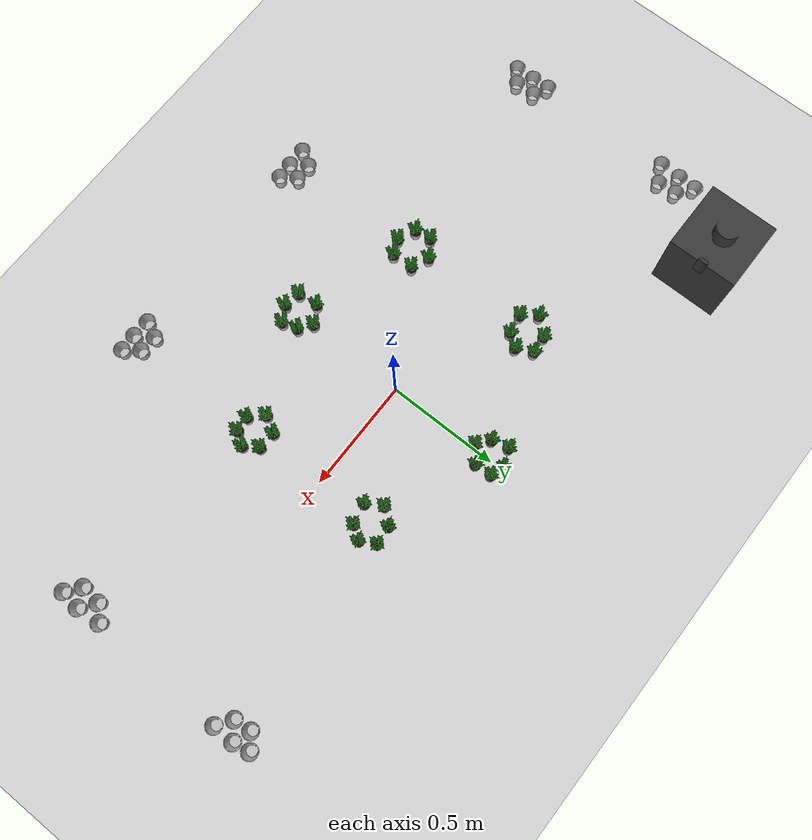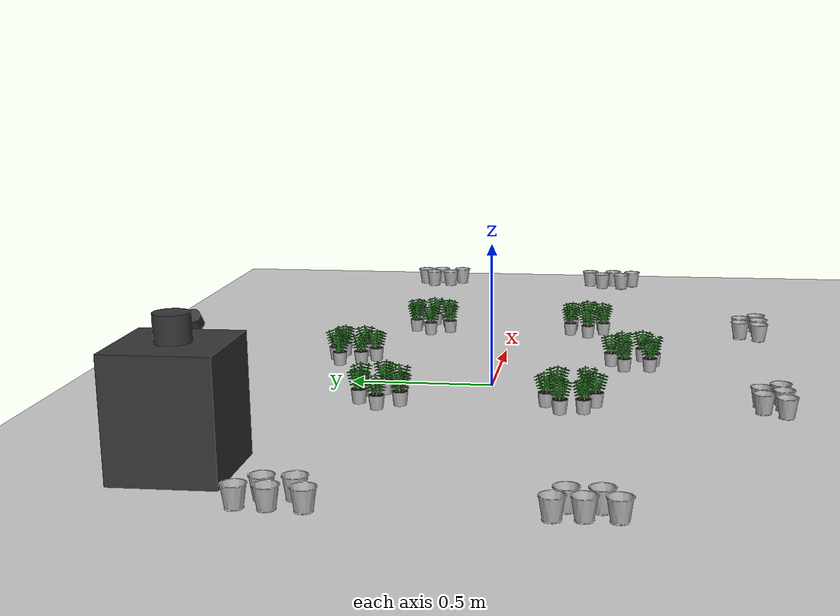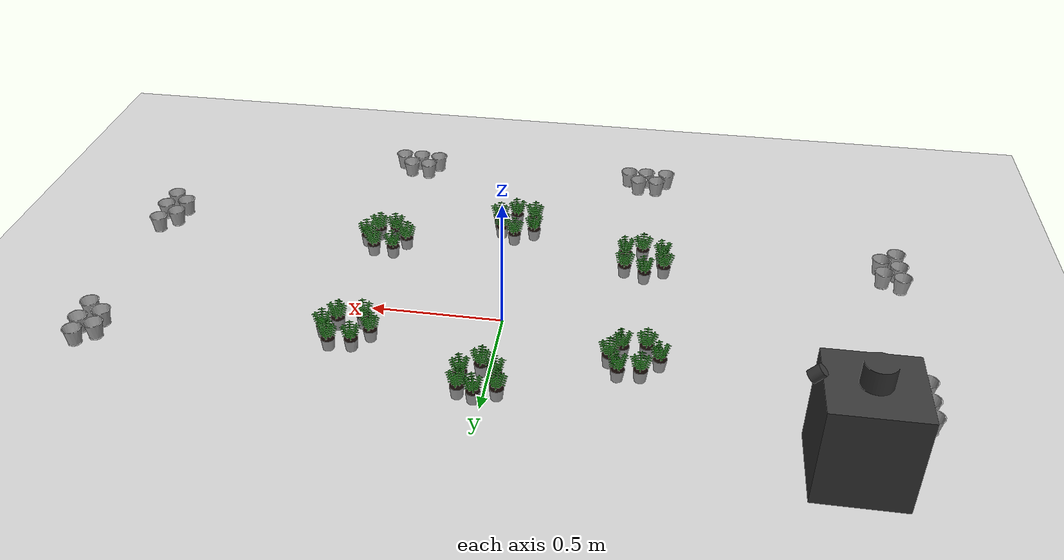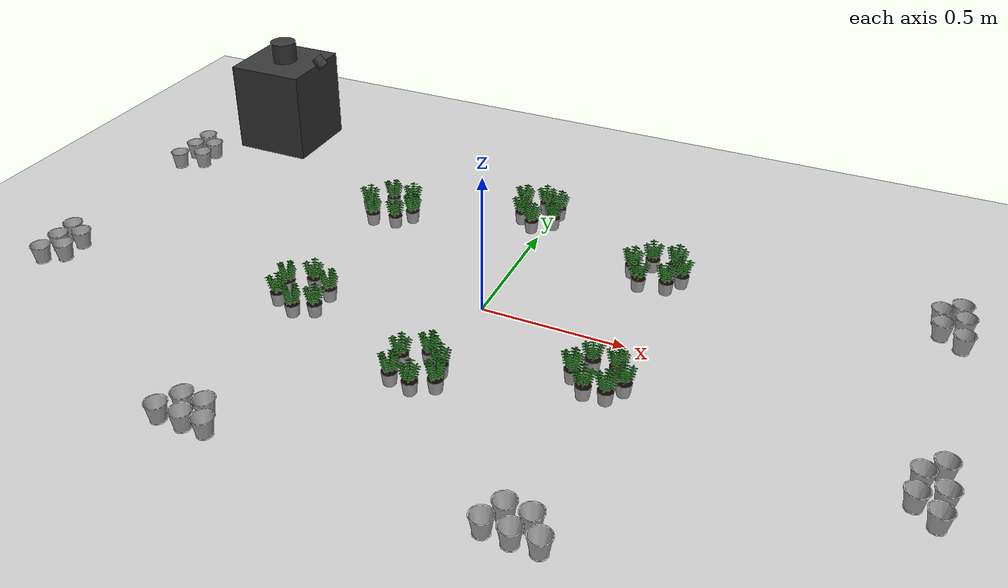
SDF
<sdf version="1.10">
 <world name="empty">
  <physics name="1ms" type="ignored">
   <max_step_size>0.001</max_step_size>
   <real_time_factor>1</real_time_factor>
   <real_time_update_rate>1000</real_time_update_rate>
  </physics>
  <plugin name="gz::sim::systems::Physics" filename="gz-sim-physics-system"/>
  <plugin name="gz::sim::systems::UserCommands" filename="gz-sim-user-commands-system"/>
  <plugin name="gz::sim::systems::SceneBroadcaster" filename="gz-sim-scene-broadcaster-system"/>
  <plugin name="gz::sim::systems::Contact" filename="gz-sim-contact-system"/>
  <plugin name="ignition::gazebo::systems::Sensors" filename="ignition-gazebo-sensors-system">
   <render_engine>ogre</render_engine>
  </plugin>
  <gravity>0 0 -9.8000000000000007</gravity>
  <magnetic_field>5.5644999999999998e-06 2.2875799999999999e-05 -4.2388400000000002e-05</magnetic_field>
  <atmosphere type="adiabatic"/>
  <scene>
   <ambient>0.400000006 0.400000006 0.400000006 1</ambient>
   <background>0.699999988 0.699999988 0.699999988 1</background>
   <shadows>true</shadows>
  </scene>
  <model name="ground_plane">
   <static>true</static>
   <link name="link">
    <collision name="collision">
     <geometry><plane><normal>0 0 1</normal><size>100 100</size></plane></geometry>
    </collision>
    <visual name="visual">
     <geometry><plane><normal>0 0 1</normal><size>100 100</size></plane></geometry>
     <material>
      <ambient>0.800000012 0.800000012 0.800000012 1</ambient>
      <diffuse>0.800000012 0.800000012 0.800000012 1</diffuse>
      <specular>0.800000012 0.800000012 0.800000012 1</specular>
     </material>
    </visual>
    <inertial>
     <mass>1</mass>
     <inertia><ixx>1</ixx><ixy>0</ixy><ixz>0</ixz><iyy>1</iyy><iyz>0</iyz><izz>1</izz></inertia>
    </inertial>
   </link>
  </model>
  <model name="pot">
   <link name="link">
    <pose>0 0 0.10000000000000001 0 0 0</pose>
    <collision name="collision">
     <geometry>
      <mesh>
       <uri>file:///home/arusso/dev/coupe/ws_0/install/champi_simulator/share/champi_simulator/models/pot/meshes/model.dae</uri>
      </mesh>
     </geometry>
    </collision>
    <visual name="visual">
     <geometry>
      <mesh>
       <uri>file:///home/arusso/dev/coupe/ws_0/install/champi_simulator/share/champi_simulator/models/pot/meshes/model.dae</uri>
      </mesh>
     </geometry>
    </visual>
    <inertial>
     <mass>1</mass>
     <inertia><ixx>1</ixx><ixy>0</ixy><ixz>0</ixz><iyy>1</iyy><iyz>0</iyz><izz>1</izz></inertia>
    </inertial>
   </link>
   <pose>-0.403499 -0.95184500000000005 -0.019989 -0.00069220900000000005 0.00014280300000000005 -4.0547600000000025e-08</pose>
   <static>false</static>
  </model>
  <model name="pot_0">
   <link name="link">
    <pose>0 0 0.10000000000000001 0 0 0</pose>
    <collision name="collision">
     <geometry>
      <mesh>
       <uri>file:///home/arusso/dev/coupe/ws_0/install/champi_simulator/share/champi_simulator/models/pot/meshes/model.dae</uri>
      </mesh>
     </geometry>
    </collision>
    <visual name="visual">
     <geometry>
      <mesh>
       <uri>file:///home/arusso/dev/coupe/ws_0/install/champi_simulator/share/champi_simulator/models/pot/meshes/model.dae</uri>
      </mesh>
     </geometry>
    </visual>
    <inertial>
     <mass>1</mass>
     <inertia><ixx>1</ixx><ixy>0</ixy><ixz>0</ixz><iyy>1</iyy><iyz>0</iyz><izz>1</izz></inertia>
    </inertial>
   </link>
   <pose>-0.47604400000000002 -0.95447199999999999 -0.019989099999999999 -0.00069144900000000001 0.00014281299999999999 -1.08879e-06</pose>
   <static>false</static>
  </model>
  <model name="pot_1">
   <link name="link">
    <pose>0 0 0.10000000000000001 0 0 0</pose>
    <collision name="collision">
     <geometry>
      <mesh>
       <uri>file:///home/arusso/dev/coupe/ws_0/install/champi_simulator/share/champi_simulator/models/pot/meshes/model.dae</uri>
      </mesh>
     </geometry>
    </collision>
    <visual name="visual">
     <geometry>
      <mesh>
       <uri>file:///home/arusso/dev/coupe/ws_0/install/champi_simulator/share/champi_simulator/models/pot/meshes/model.dae</uri>
      </mesh>
     </geometry>
    </visual>
    <inertial>
     <mass>1</mass>
     <inertia><ixx>1</ixx><ixy>0</ixy><ixz>0</ixz><iyy>1</iyy><iyz>0</iyz><izz>1</izz></inertia>
    </inertial>
   </link>
   <pose>-0.55947499999999994 -0.95512300000000006 -0.019989 -0.00069220900000000005 0.00014280300000000005 -4.0547600000000025e-08</pose>
   <static>false</static>
  </model>
  <model name="pot_2">
   <link name="link">
    <pose>0 0 0.10000000000000001 0 0 0</pose>
    <collision name="collision">
     <geometry>
      <mesh>
       <uri>file:///home/arusso/dev/coupe/ws_0/install/champi_simulator/share/champi_simulator/models/pot/meshes/model.dae</uri>
      </mesh>
     </geometry>
    </collision>
    <visual name="visual">
     <geometry>
      <mesh>
       <uri>file:///home/arusso/dev/coupe/ws_0/install/champi_simulator/share/champi_simulator/models/pot/meshes/model.dae</uri>
      </mesh>
     </geometry>
    </visual>
    <inertial>
     <mass>1</mass>
     <inertia><ixx>1</ixx><ixy>0</ixy><ixz>0</ixz><iyy>1</iyy><iyz>0</iyz><izz>1</izz></inertia>
    </inertial>
   </link>
   <pose>-0.52089099999999999 -0.88975899999999997 -0.019989 -0.00069220900000000005 0.00014280300000000005 -4.0547600000000025e-08</pose>
   <static>false</static>
  </model>
  <model name="pot_3">
   <link name="link">
    <pose>0 0 0.10000000000000001 0 0 0</pose>
    <collision name="collision">
     <geometry>
      <mesh>
       <uri>file:///home/arusso/dev/coupe/ws_0/install/champi_simulator/share/champi_simulator/models/pot/meshes/model.dae</uri>
      </mesh>
     </geometry>
    </collision>
    <visual name="visual">
     <geometry>
      <mesh>
       <uri>file:///home/arusso/dev/coupe/ws_0/install/champi_simulator/share/champi_simulator/models/pot/meshes/model.dae</uri>
      </mesh>
     </geometry>
    </visual>
    <inertial>
     <mass>1</mass>
     <inertia><ixx>1</ixx><ixy>0</ixy><ixz>0</ixz><iyy>1</iyy><iyz>0</iyz><izz>1</izz></inertia>
    </inertial>
   </link>
   <pose>-0.446768 -0.88781500000000002 -0.019989 -0.00069220900000000005 0.00014280300000000005 -4.0547600000000025e-08</pose>
   <static>false</static>
  </model>
  <model name="pot_5">
   <link name="link">
    <pose>0 0 0.10000000000000001 0 0 0</pose>
    <collision name="collision">
     <geometry>
      <mesh>
       <uri>file:///home/arusso/dev/coupe/ws_0/install/champi_simulator/share/champi_simulator/models/pot/meshes/model.dae</uri>
      </mesh>
     </geometry>
    </collision>
    <visual name="visual">
     <geometry>
      <mesh>
       <uri>file:///home/arusso/dev/coupe/ws_0/install/champi_simulator/share/champi_simulator/models/pot/meshes/model.dae</uri>
      </mesh>
     </geometry>
    </visual>
    <inertial>
     <mass>1</mass>
     <inertia><ixx>1</ixx><ixy>0</ixy><ixz>0</ixz><iyy>1</iyy><iyz>0</iyz><izz>1</izz></inertia>
    </inertial>
   </link>
   <pose>-1.39436 -0.33459699999999998 -0.019989 -0.00069220900000000005 0.00014280300000000005 -4.0547600000000025e-08</pose>
   <static>false</static>
  </model>
  <model name="pot_6">
   <link name="link">
    <pose>0 0 0.10000000000000001 0 0 0</pose>
    <collision name="collision">
     <geometry>
      <mesh>
       <uri>file:///home/arusso/dev/coupe/ws_0/install/champi_simulator/share/champi_simulator/models/pot/meshes/model.dae</uri>
      </mesh>
     </geometry>
    </collision>
    <visual name="visual">
     <geometry>
      <mesh>
       <uri>file:///home/arusso/dev/coupe/ws_0/install/champi_simulator/share/champi_simulator/models/pot/meshes/model.dae</uri>
      </mesh>
     </geometry>
    </visual>
    <inertial>
     <mass>1</mass>
     <inertia><ixx>1</ixx><ixy>0</ixy><ixz>0</ixz><iyy>1</iyy><iyz>0</iyz><izz>1</izz></inertia>
    </inertial>
   </link>
   <pose>-1.3934500000000001 -0.422989 -0.019989 -0.00069220900000000005 0.00014280300000000005 -4.0547600000000025e-08</pose>
   <static>false</static>
  </model>
  <model name="pot_7">
   <link name="link">
    <pose>0 0 0.10000000000000001 0 0 0</pose>
    <collision name="collision">
     <geometry>
      <mesh>
       <uri>file:///home/arusso/dev/coupe/ws_0/install/champi_simulator/share/champi_simulator/models/pot/meshes/model.dae</uri>
      </mesh>
     </geometry>
    </collision>
    <visual name="visual">
     <geometry>
      <mesh>
       <uri>file:///home/arusso/dev/coupe/ws_0/install/champi_simulator/share/champi_simulator/models/pot/meshes/model.dae</uri>
      </mesh>
     </geometry>
    </visual>
    <inertial>
     <mass>1</mass>
     <inertia><ixx>1</ixx><ixy>0</ixy><ixz>0</ixz><iyy>1</iyy><iyz>0</iyz><izz>1</izz></inertia>
    </inertial>
   </link>
   <pose>-1.45492 -0.38141199999999997 -0.0199889 -0.00069295299999999995 0.00014295299999999994 0.00021204300000000006</pose>
   <static>false</static>
  </model>
  <model name="pot_8">
   <link name="link">
    <pose>0 0 0.10000000000000001 0 0 0</pose>
    <collision name="collision">
     <geometry>
      <mesh>
       <uri>file:///home/arusso/dev/coupe/ws_0/install/champi_simulator/share/champi_simulator/models/pot/meshes/model.dae</uri>
      </mesh>
     </geometry>
    </collision>
    <visual name="visual">
     <geometry>
      <mesh>
       <uri>file:///home/arusso/dev/coupe/ws_0/install/champi_simulator/share/champi_simulator/models/pot/meshes/model.dae</uri>
      </mesh>
     </geometry>
    </visual>
    <inertial>
     <mass>1</mass>
     <inertia><ixx>1</ixx><ixy>0</ixy><ixz>0</ixz><iyy>1</iyy><iyz>0</iyz><izz>1</izz></inertia>
    </inertial>
   </link>
   <pose>-1.45387 -0.46632400000000002 -0.019989 -0.00069220900000000005 0.00014280300000000005 -4.0547600000000025e-08</pose>
   <static>false</static>
  </model>
  <model name="pot_9">
   <link name="link">
    <pose>0 0 0.10000000000000001 0 0 0</pose>
    <collision name="collision">
     <geometry>
      <mesh>
       <uri>file:///home/arusso/dev/coupe/ws_0/install/champi_simulator/share/champi_simulator/models/pot/meshes/model.dae</uri>
      </mesh>
     </geometry>
    </collision>
    <visual name="visual">
     <geometry>
      <mesh>
       <uri>file:///home/arusso/dev/coupe/ws_0/install/champi_simulator/share/champi_simulator/models/pot/meshes/model.dae</uri>
      </mesh>
     </geometry>
    </visual>
    <inertial>
     <mass>1</mass>
     <inertia><ixx>1</ixx><ixy>0</ixy><ixz>0</ixz><iyy>1</iyy><iyz>0</iyz><izz>1</izz></inertia>
    </inertial>
   </link>
   <pose>-1.4593499999999999 -0.30384 -0.019989 -0.00069220900000000005 0.00014280300000000005 -4.0547600000000025e-08</pose>
   <static>false</static>
  </model>
  <model name="pot_10">
   <link name="link">
    <pose>0 0 0.10000000000000001 0 0 0</pose>
    <collision name="collision">
     <geometry>
      <mesh>
       <uri>file:///home/arusso/dev/coupe/ws_0/install/champi_simulator/share/champi_simulator/models/pot/meshes/model.dae</uri>
      </mesh>
     </geometry>
    </collision>
    <visual name="visual">
     <geometry>
      <mesh>
       <uri>file:///home/arusso/dev/coupe/ws_0/install/champi_simulator/share/champi_simulator/models/pot/meshes/model.dae</uri>
      </mesh>
     </geometry>
    </visual>
    <inertial>
     <mass>1</mass>
     <inertia><ixx>1</ixx><ixy>0</ixy><ixz>0</ixz><iyy>1</iyy><iyz>0</iyz><izz>1</izz></inertia>
    </inertial>
   </link>
   <pose>-1.46313 0.29849799999999999 -0.019989 -0.00069220900000000005 0.00014280300000000005 -4.0547600000000025e-08</pose>
   <static>false</static>
  </model>
  <model name="pot_11">
   <link name="link">
    <pose>0 0 0.10000000000000001 0 0 0</pose>
    <collision name="collision">
     <geometry>
      <mesh>
       <uri>file:///home/arusso/dev/coupe/ws_0/install/champi_simulator/share/champi_simulator/models/pot/meshes/model.dae</uri>
      </mesh>
     </geometry>
    </collision>
    <visual name="visual">
     <geometry>
      <mesh>
       <uri>file:///home/arusso/dev/coupe/ws_0/install/champi_simulator/share/champi_simulator/models/pot/meshes/model.dae</uri>
      </mesh>
     </geometry>
    </visual>
    <inertial>
     <mass>1</mass>
     <inertia><ixx>1</ixx><ixy>0</ixy><ixz>0</ixz><iyy>1</iyy><iyz>0</iyz><izz>1</izz></inertia>
    </inertial>
   </link>
   <pose>-1.4589799999999999 0.39272800000000002 -0.0199889 -0.00069269900000000018 0.00014398599999999995 -0.0041653999999999997</pose>
   <static>false</static>
  </model>
  <model name="pot_12">
   <link name="link">
    <pose>0 0 0.10000000000000001 0 0 0</pose>
    <collision name="collision">
     <geometry>
      <mesh>
       <uri>file:///home/arusso/dev/coupe/ws_0/install/champi_simulator/share/champi_simulator/models/pot/meshes/model.dae</uri>
      </mesh>
     </geometry>
    </collision>
    <visual name="visual">
     <geometry>
      <mesh>
       <uri>file:///home/arusso/dev/coupe/ws_0/install/champi_simulator/share/champi_simulator/models/pot/meshes/model.dae</uri>
      </mesh>
     </geometry>
    </visual>
    <inertial>
     <mass>1</mass>
     <inertia><ixx>1</ixx><ixy>0</ixy><ixz>0</ixz><iyy>1</iyy><iyz>0</iyz><izz>1</izz></inertia>
    </inertial>
   </link>
   <pose>-1.4570399999999999 0.47462300000000002 -0.019989 -0.00069220900000000005 0.00014280300000000005 -4.0547600000000025e-08</pose>
   <static>false</static>
  </model>
  <model name="pot_13">
   <link name="link">
    <pose>0 0 0.10000000000000001 0 0 0</pose>
    <collision name="collision">
     <geometry>
      <mesh>
       <uri>file:///home/arusso/dev/coupe/ws_0/install/champi_simulator/share/champi_simulator/models/pot/meshes/model.dae</uri>
      </mesh>
     </geometry>
    </collision>
    <visual name="visual">
     <geometry>
      <mesh>
       <uri>file:///home/arusso/dev/coupe/ws_0/install/champi_simulator/share/champi_simulator/models/pot/meshes/model.dae</uri>
      </mesh>
     </geometry>
    </visual>
    <inertial>
     <mass>1</mass>
     <inertia><ixx>1</ixx><ixy>0</ixy><ixz>0</ixz><iyy>1</iyy><iyz>0</iyz><izz>1</izz></inertia>
    </inertial>
   </link>
   <pose>-1.38368 0.339557 -0.019989 -0.00069220900000000005 0.00014280300000000005 -4.0547600000000025e-08</pose>
   <static>false</static>
  </model>
  <model name="pot_14">
   <link name="link">
    <pose>0 0 0.10000000000000001 0 0 0</pose>
    <collision name="collision">
     <geometry>
      <mesh>
       <uri>file:///home/arusso/dev/coupe/ws_0/install/champi_simulator/share/champi_simulator/models/pot/meshes/model.dae</uri>
      </mesh>
     </geometry>
    </collision>
    <visual name="visual">
     <geometry>
      <mesh>
       <uri>file:///home/arusso/dev/coupe/ws_0/install/champi_simulator/share/champi_simulator/models/pot/meshes/model.dae</uri>
      </mesh>
     </geometry>
    </visual>
    <inertial>
     <mass>1</mass>
     <inertia><ixx>1</ixx><ixy>0</ixy><ixz>0</ixz><iyy>1</iyy><iyz>0</iyz><izz>1</izz></inertia>
    </inertial>
   </link>
   <pose>-1.3895200000000001 0.42288199999999998 -0.019989 -0.00069220900000000005 0.00014280300000000005 -4.0547600000000025e-08</pose>
   <static>false</static>
  </model>
  <model name="pot_15">
   <link name="link">
    <pose>0 0 0.10000000000000001 0 0 0</pose>
    <collision name="collision">
     <geometry>
      <mesh>
       <uri>file:///home/arusso/dev/coupe/ws_0/install/champi_simulator/share/champi_simulator/models/pot/meshes/model.dae</uri>
      </mesh>
     </geometry>
    </collision>
    <visual name="visual">
     <geometry>
      <mesh>
       <uri>file:///home/arusso/dev/coupe/ws_0/install/champi_simulator/share/champi_simulator/models/pot/meshes/model.dae</uri>
      </mesh>
     </geometry>
    </visual>
    <inertial>
     <mass>1</mass>
     <inertia><ixx>1</ixx><ixy>0</ixy><ixz>0</ixz><iyy>1</iyy><iyz>0</iyz><izz>1</izz></inertia>
    </inertial>
   </link>
   <pose>1.4501900000000001 0.46426099999999998 -0.019989 -0.00069220900000000005 0.00014280300000000005 -4.0547600000000025e-08</pose>
   <static>false</static>
  </model>
  <model name="pot_16">
   <link name="link">
    <pose>0 0 0.10000000000000001 0 0 0</pose>
    <collision name="collision">
     <geometry>
      <mesh>
       <uri>file:///home/arusso/dev/coupe/ws_0/install/champi_simulator/share/champi_simulator/models/pot/meshes/model.dae</uri>
      </mesh>
     </geometry>
    </collision>
    <visual name="visual">
     <geometry>
      <mesh>
       <uri>file:///home/arusso/dev/coupe/ws_0/install/champi_simulator/share/champi_simulator/models/pot/meshes/model.dae</uri>
      </mesh>
     </geometry>
    </visual>
    <inertial>
     <mass>1</mass>
     <inertia><ixx>1</ixx><ixy>0</ixy><ixz>0</ixz><iyy>1</iyy><iyz>0</iyz><izz>1</izz></inertia>
    </inertial>
   </link>
   <pose>1.4631799999999999 0.39277099999999998 -0.0199889 -0.00069345600000000017 0.00014240400000000011 0.0018851600000000001</pose>
   <static>false</static>
  </model>
  <model name="pot_17">
   <link name="link">
    <pose>0 0 0.10000000000000001 0 0 0</pose>
    <collision name="collision">
     <geometry>
      <mesh>
       <uri>file:///home/arusso/dev/coupe/ws_0/install/champi_simulator/share/champi_simulator/models/pot/meshes/model.dae</uri>
      </mesh>
     </geometry>
    </collision>
    <visual name="visual">
     <geometry>
      <mesh>
       <uri>file:///home/arusso/dev/coupe/ws_0/install/champi_simulator/share/champi_simulator/models/pot/meshes/model.dae</uri>
      </mesh>
     </geometry>
    </visual>
    <inertial>
     <mass>1</mass>
     <inertia><ixx>1</ixx><ixy>0</ixy><ixz>0</ixz><iyy>1</iyy><iyz>0</iyz><izz>1</izz></inertia>
    </inertial>
   </link>
   <pose>1.4628300000000001 0.299319 -0.019989 -0.00069220900000000005 0.00014280300000000005 -4.0547600000000025e-08</pose>
   <static>false</static>
  </model>
  <model name="pot_18">
   <link name="link">
    <pose>0 0 0.10000000000000001 0 0 0</pose>
    <collision name="collision">
     <geometry>
      <mesh>
       <uri>file:///home/arusso/dev/coupe/ws_0/install/champi_simulator/share/champi_simulator/models/pot/meshes/model.dae</uri>
      </mesh>
     </geometry>
    </collision>
    <visual name="visual">
     <geometry>
      <mesh>
       <uri>file:///home/arusso/dev/coupe/ws_0/install/champi_simulator/share/champi_simulator/models/pot/meshes/model.dae</uri>
      </mesh>
     </geometry>
    </visual>
    <inertial>
     <mass>1</mass>
     <inertia><ixx>1</ixx><ixy>0</ixy><ixz>0</ixz><iyy>1</iyy><iyz>0</iyz><izz>1</izz></inertia>
    </inertial>
   </link>
   <pose>1.3919299999999999 0.41950300000000001 -0.019989 -0.00069220900000000005 0.00014280300000000005 -4.0547600000000025e-08</pose>
   <static>false</static>
  </model>
  <model name="pot_19">
   <link name="link">
    <pose>0 0 0.10000000000000001 0 0 0</pose>
    <collision name="collision">
     <geometry>
      <mesh>
       <uri>file:///home/arusso/dev/coupe/ws_0/install/champi_simulator/share/champi_simulator/models/pot/meshes/model.dae</uri>
      </mesh>
     </geometry>
    </collision>
    <visual name="visual">
     <geometry>
      <mesh>
       <uri>file:///home/arusso/dev/coupe/ws_0/install/champi_simulator/share/champi_simulator/models/pot/meshes/model.dae</uri>
      </mesh>
     </geometry>
    </visual>
    <inertial>
     <mass>1</mass>
     <inertia><ixx>1</ixx><ixy>0</ixy><ixz>0</ixz><iyy>1</iyy><iyz>0</iyz><izz>1</izz></inertia>
    </inertial>
   </link>
   <pose>1.3986799999999999 0.34415899999999999 -0.019989 -0.00069220900000000005 0.00014280300000000005 -4.0547600000000025e-08</pose>
   <static>false</static>
  </model>
  <model name="pot_20">
   <link name="link">
    <pose>0 0 0.10000000000000001 0 0 0</pose>
    <collision name="collision">
     <geometry>
      <mesh>
       <uri>file:///home/arusso/dev/coupe/ws_0/install/champi_simulator/share/champi_simulator/models/pot/meshes/model.dae</uri>
      </mesh>
     </geometry>
    </collision>
    <visual name="visual">
     <geometry>
      <mesh>
       <uri>file:///home/arusso/dev/coupe/ws_0/install/champi_simulator/share/champi_simulator/models/pot/meshes/model.dae</uri>
      </mesh>
     </geometry>
    </visual>
    <inertial>
     <mass>1</mass>
     <inertia><ixx>1</ixx><ixy>0</ixy><ixz>0</ixz><iyy>1</iyy><iyz>0</iyz><izz>1</izz></inertia>
    </inertial>
   </link>
   <pose>0.58666300000000005 -0.96050400000000002 -0.019989 -0.00069220900000000005 0.00014280300000000005 -4.0547600000000025e-08</pose>
   <static>false</static>
  </model>
  <model name="pot_21">
   <link name="link">
    <pose>0 0 0.10000000000000001 0 0 0</pose>
    <collision name="collision">
     <geometry>
      <mesh>
       <uri>file:///home/arusso/dev/coupe/ws_0/install/champi_simulator/share/champi_simulator/models/pot/meshes/model.dae</uri>
      </mesh>
     </geometry>
    </collision>
    <visual name="visual">
     <geometry>
      <mesh>
       <uri>file:///home/arusso/dev/coupe/ws_0/install/champi_simulator/share/champi_simulator/models/pot/meshes/model.dae</uri>
      </mesh>
     </geometry>
    </visual>
    <inertial>
     <mass>1</mass>
     <inertia><ixx>1</ixx><ixy>0</ixy><ixz>0</ixz><iyy>1</iyy><iyz>0</iyz><izz>1</izz></inertia>
    </inertial>
   </link>
   <pose>0.51073000000000002 -0.96303499999999997 -0.0199889 -0.00069275300000000005 0.00014289600000000005 -3.8064700000000008e-06</pose>
   <static>false</static>
  </model>
  <model name="pot_22">
   <link name="link">
    <pose>0 0 0.10000000000000001 0 0 0</pose>
    <collision name="collision">
     <geometry>
      <mesh>
       <uri>file:///home/arusso/dev/coupe/ws_0/install/champi_simulator/share/champi_simulator/models/pot/meshes/model.dae</uri>
      </mesh>
     </geometry>
    </collision>
    <visual name="visual">
     <geometry>
      <mesh>
       <uri>file:///home/arusso/dev/coupe/ws_0/install/champi_simulator/share/champi_simulator/models/pot/meshes/model.dae</uri>
      </mesh>
     </geometry>
    </visual>
    <inertial>
     <mass>1</mass>
     <inertia><ixx>1</ixx><ixy>0</ixy><ixz>0</ixz><iyy>1</iyy><iyz>0</iyz><izz>1</izz></inertia>
    </inertial>
   </link>
   <pose>0.43281500000000001 -0.95924200000000004 -0.019989 -0.00069220900000000005 0.00014280300000000005 -4.0547600000000025e-08</pose>
   <static>false</static>
  </model>
  <model name="pot_23">
   <link name="link">
    <pose>0 0 0.10000000000000001 0 0 0</pose>
    <collision name="collision">
     <geometry>
      <mesh>
       <uri>file:///home/arusso/dev/coupe/ws_0/install/champi_simulator/share/champi_simulator/models/pot/meshes/model.dae</uri>
      </mesh>
     </geometry>
    </collision>
    <visual name="visual">
     <geometry>
      <mesh>
       <uri>file:///home/arusso/dev/coupe/ws_0/install/champi_simulator/share/champi_simulator/models/pot/meshes/model.dae</uri>
      </mesh>
     </geometry>
    </visual>
    <inertial>
     <mass>1</mass>
     <inertia><ixx>1</ixx><ixy>0</ixy><ixz>0</ixz><iyy>1</iyy><iyz>0</iyz><izz>1</izz></inertia>
    </inertial>
   </link>
   <pose>0.54138699999999995 -0.89774799999999999 -0.019989 -0.00069220900000000005 0.00014280300000000005 -4.0547600000000025e-08</pose>
   <static>false</static>
  </model>
  <model name="pot_24">
   <link name="link">
    <pose>0 0 0.10000000000000001 0 0 0</pose>
    <collision name="collision">
     <geometry>
      <mesh>
       <uri>file:///home/arusso/dev/coupe/ws_0/install/champi_simulator/share/champi_simulator/models/pot/meshes/model.dae</uri>
      </mesh>
     </geometry>
    </collision>
    <visual name="visual">
     <geometry>
      <mesh>
       <uri>file:///home/arusso/dev/coupe/ws_0/install/champi_simulator/share/champi_simulator/models/pot/meshes/model.dae</uri>
      </mesh>
     </geometry>
    </visual>
    <inertial>
     <mass>1</mass>
     <inertia><ixx>1</ixx><ixy>0</ixy><ixz>0</ixz><iyy>1</iyy><iyz>0</iyz><izz>1</izz></inertia>
    </inertial>
   </link>
   <pose>0.46546399999999999 -0.89145600000000003 -0.019989 -0.00069220900000000005 0.00014280300000000005 -4.0547600000000025e-08</pose>
   <static>false</static>
  </model>
  <model name="pot_29">
   <link name="link">
    <pose>0 0 0.10000000000000001 0 0 0</pose>
    <collision name="collision">
     <geometry>
      <mesh>
       <uri>file:///home/arusso/dev/coupe/ws_0/install/champi_simulator/share/champi_simulator/models/pot/meshes/model.dae</uri>
      </mesh>
     </geometry>
    </collision>
    <visual name="visual">
     <geometry>
      <mesh>
       <uri>file:///home/arusso/dev/coupe/ws_0/install/champi_simulator/share/champi_simulator/models/pot/meshes/model.dae</uri>
      </mesh>
     </geometry>
    </visual>
    <inertial>
     <mass>1</mass>
     <inertia><ixx>1</ixx><ixy>0</ixy><ixz>0</ixz><iyy>1</iyy><iyz>0</iyz><izz>1</izz></inertia>
    </inertial>
   </link>
   <pose>1.4604999999999999 -0.39635399999999998 -0.019989 -0.00069220900000000005 0.00014280300000000005 -4.0547600000000025e-08</pose>
   <static>false</static>
  </model>
  <model name="pot_30">
   <link name="link">
    <pose>0 0 0.10000000000000001 0 0 0</pose>
    <collision name="collision">
     <geometry>
      <mesh>
       <uri>file:///home/arusso/dev/coupe/ws_0/install/champi_simulator/share/champi_simulator/models/pot/meshes/model.dae</uri>
      </mesh>
     </geometry>
    </collision>
    <visual name="visual">
     <geometry>
      <mesh>
       <uri>file:///home/arusso/dev/coupe/ws_0/install/champi_simulator/share/champi_simulator/models/pot/meshes/model.dae</uri>
      </mesh>
     </geometry>
    </visual>
    <inertial>
     <mass>1</mass>
     <inertia><ixx>1</ixx><ixy>0</ixy><ixz>0</ixz><iyy>1</iyy><iyz>0</iyz><izz>1</izz></inertia>
    </inertial>
   </link>
   <pose>1.4497 -0.48125200000000001 -0.019989 -0.00069220900000000005 0.00014280300000000005 -4.0547600000000025e-08</pose>
   <static>false</static>
  </model>
  <model name="pot_31">
   <link name="link">
    <pose>0 0 0.10000000000000001 0 0 0</pose>
    <collision name="collision">
     <geometry>
      <mesh>
       <uri>file:///home/arusso/dev/coupe/ws_0/install/champi_simulator/share/champi_simulator/models/pot/meshes/model.dae</uri>
      </mesh>
     </geometry>
    </collision>
    <visual name="visual">
     <geometry>
      <mesh>
       <uri>file:///home/arusso/dev/coupe/ws_0/install/champi_simulator/share/champi_simulator/models/pot/meshes/model.dae</uri>
      </mesh>
     </geometry>
    </visual>
    <inertial>
     <mass>1</mass>
     <inertia><ixx>1</ixx><ixy>0</ixy><ixz>0</ixz><iyy>1</iyy><iyz>0</iyz><izz>1</izz></inertia>
    </inertial>
   </link>
   <pose>1.3979200000000001 -0.347551 -0.0199889 -0.00069334400000000003 0.00014329600000000006 -0.049522400000000015</pose>
   <static>false</static>
  </model>
  <model name="pot_32">
   <link name="link">
    <pose>0 0 0.10000000000000001 0 0 0</pose>
    <collision name="collision">
     <geometry>
      <mesh>
       <uri>file:///home/arusso/dev/coupe/ws_0/install/champi_simulator/share/champi_simulator/models/pot/meshes/model.dae</uri>
      </mesh>
     </geometry>
    </collision>
    <visual name="visual">
     <geometry>
      <mesh>
       <uri>file:///home/arusso/dev/coupe/ws_0/install/champi_simulator/share/champi_simulator/models/pot/meshes/model.dae</uri>
      </mesh>
     </geometry>
    </visual>
    <inertial>
     <mass>1</mass>
     <inertia><ixx>1</ixx><ixy>0</ixy><ixz>0</ixz><iyy>1</iyy><iyz>0</iyz><izz>1</izz></inertia>
    </inertial>
   </link>
   <pose>1.3893899999999999 -0.43281500000000001 -0.019989 -0.00069220900000000005 0.00014280300000000005 -4.0547600000000025e-08</pose>
   <static>false</static>
  </model>
  <model name="pot_4">
   <link name="link">
    <pose>0 0 0.10000000000000001 0 0 0</pose>
    <collision name="collision">
     <geometry>
      <mesh>
       <uri>file:///home/arusso/dev/coupe/ws_0/install/champi_simulator/share/champi_simulator/models/pot/meshes/model.dae</uri>
      </mesh>
     </geometry>
    </collision>
    <visual name="visual">
     <geometry>
      <mesh>
       <uri>file:///home/arusso/dev/coupe/ws_0/install/champi_simulator/share/champi_simulator/models/pot/meshes/model.dae</uri>
      </mesh>
     </geometry>
    </visual>
    <inertial>
     <mass>1</mass>
     <inertia><ixx>1</ixx><ixy>0</ixy><ixz>0</ixz><iyy>1</iyy><iyz>0</iyz><izz>1</izz></inertia>
    </inertial>
   </link>
   <pose>1.4515499999999999 -0.29249799999999998 -0.019989 -0.00069220900000000005 0.00014280300000000005 -4.0547600000000025e-08</pose>
   <static>false</static>
  </model>
  <model name="plante_resistante">
   <link name="link">
    <pose>0 0 0.10000000000000001 0 0 0</pose>
    <collision name="collision">
     <geometry>
      <mesh>
       <uri>file:///home/arusso/dev/coupe/ws_0/install/champi_simulator/share/champi_simulator/models/plante_resistante/meshes/model.dae</uri>
      </mesh>
     </geometry>
    </collision>
    <visual name="visual">
     <geometry>
      <mesh>
       <uri>file:///home/arusso/dev/coupe/ws_0/install/champi_simulator/share/champi_simulator/models/plante_resistante/meshes/model.dae</uri>
      </mesh>
     </geometry>
    </visual>
    <inertial>
     <mass>1</mass>
     <inertia><ixx>1</ixx><ixy>0</ixy><ixz>0</ixz><iyy>1</iyy><iyz>0</iyz><izz>1</izz></inertia>
    </inertial>
   </link>
   <pose>0.58933000000000002 -0.31569799999999998 -0.019975900000000001 3.8603699999999984e-05 -0.0020328400000000002 -1.2490100000000001e-06</pose>
   <static>false</static>
  </model>
  <model name="plante_resistante_0">
   <link name="link">
    <pose>0 0 0.10000000000000001 0 0 0</pose>
    <collision name="collision">
     <geometry>
      <mesh>
       <uri>file:///home/arusso/dev/coupe/ws_0/install/champi_simulator/share/champi_simulator/models/plante_resistante/meshes/model.dae</uri>
      </mesh>
     </geometry>
    </collision>
    <visual name="visual">
     <geometry>
      <mesh>
       <uri>file:///home/arusso/dev/coupe/ws_0/install/champi_simulator/share/champi_simulator/models/plante_resistante/meshes/model.dae</uri>
      </mesh>
     </geometry>
    </visual>
    <inertial>
     <mass>1</mass>
     <inertia><ixx>1</ixx><ixy>0</ixy><ixz>0</ixz><iyy>1</iyy><iyz>0</iyz><izz>1</izz></inertia>
    </inertial>
   </link>
   <pose>0.486674 -0.37622499999999998 -0.019975900000000001 3.8603699999999984e-05 -0.0020328400000000002 -1.2490100000000001e-06</pose>
   <static>false</static>
  </model>
  <model name="plante_resistante_1">
   <link name="link">
    <pose>0 0 0.10000000000000001 0 0 0</pose>
    <collision name="collision">
     <geometry>
      <mesh>
       <uri>file:///home/arusso/dev/coupe/ws_0/install/champi_simulator/share/champi_simulator/models/plante_resistante/meshes/model.dae</uri>
      </mesh>
     </geometry>
    </collision>
    <visual name="visual">
     <geometry>
      <mesh>
       <uri>file:///home/arusso/dev/coupe/ws_0/install/champi_simulator/share/champi_simulator/models/plante_resistante/meshes/model.dae</uri>
      </mesh>
     </geometry>
    </visual>
    <inertial>
     <mass>1</mass>
     <inertia><ixx>1</ixx><ixy>0</ixy><ixz>0</ixz><iyy>1</iyy><iyz>0</iyz><izz>1</izz></inertia>
    </inertial>
   </link>
   <pose>0.47190300000000002 -0.25067699999999998 -0.019975900000000001 3.8603699999999984e-05 -0.0020328400000000002 -1.2490100000000001e-06</pose>
   <static>false</static>
  </model>
  <model name="plante_fragile">
   <link name="link">
    <pose>0 0 0.10000000000000001 0 0 0</pose>
    <collision name="collision">
     <geometry>
      <mesh>
       <uri>file:///home/arusso/dev/coupe/ws_0/install/champi_simulator/share/champi_simulator/models/plante_fragile/meshes/model.dae</uri>
      </mesh>
     </geometry>
    </collision>
    <visual name="visual">
     <geometry>
      <mesh>
       <uri>file:///home/arusso/dev/coupe/ws_0/install/champi_simulator/share/champi_simulator/models/plante_fragile/meshes/model.dae</uri>
      </mesh>
     </geometry>
    </visual>
    <inertial>
     <mass>1</mass>
     <inertia><ixx>1</ixx><ixy>0</ixy><ixz>0</ixz><iyy>1</iyy><iyz>0</iyz><izz>1</izz></inertia>
    </inertial>
   </link>
   <pose>0.55256899999999998 -0.36994500000000002 -0.019975900000000001 3.8603699999999984e-05 -0.0020328400000000002 -1.2490100000000001e-06</pose>
   <static>false</static>
  </model>
  <model name="plante_fragile_0">
   <link name="link">
    <pose>0 0 0.10000000000000001 0 0 0</pose>
    <collision name="collision">
     <geometry>
      <mesh>
       <uri>file:///home/arusso/dev/coupe/ws_0/install/champi_simulator/share/champi_simulator/models/plante_fragile/meshes/model.dae</uri>
      </mesh>
     </geometry>
    </collision>
    <visual name="visual">
     <geometry>
      <mesh>
       <uri>file:///home/arusso/dev/coupe/ws_0/install/champi_simulator/share/champi_simulator/models/plante_fragile/meshes/model.dae</uri>
      </mesh>
     </geometry>
    </visual>
    <inertial>
     <mass>1</mass>
     <inertia><ixx>1</ixx><ixy>0</ixy><ixz>0</ixz><iyy>1</iyy><iyz>0</iyz><izz>1</izz></inertia>
    </inertial>
   </link>
   <pose>0.54969800000000002 -0.25431500000000001 -0.019975900000000001 3.8603699999999984e-05 -0.0020328400000000002 -1.2490100000000001e-06</pose>
   <static>false</static>
  </model>
  <model name="plante_fragile_1">
   <link name="link">
    <pose>0 0 0.10000000000000001 0 0 0</pose>
    <collision name="collision">
     <geometry>
      <mesh>
       <uri>file:///home/arusso/dev/coupe/ws_0/install/champi_simulator/share/champi_simulator/models/plante_fragile/meshes/model.dae</uri>
      </mesh>
     </geometry>
    </collision>
    <visual name="visual">
     <geometry>
      <mesh>
       <uri>file:///home/arusso/dev/coupe/ws_0/install/champi_simulator/share/champi_simulator/models/plante_fragile/meshes/model.dae</uri>
      </mesh>
     </geometry>
    </visual>
    <inertial>
     <mass>1</mass>
     <inertia><ixx>1</ixx><ixy>0</ixy><ixz>0</ixz><iyy>1</iyy><iyz>0</iyz><izz>1</izz></inertia>
    </inertial>
   </link>
   <pose>0.43286200000000002 -0.31884899999999999 -0.019975900000000001 3.8603699999999984e-05 -0.0020328400000000002 -1.2490100000000001e-06</pose>
   <static>false</static>
  </model>
  <model name="plante_fragile_2">
   <link name="link">
    <pose>0 0 0.10000000000000001 0 0 0</pose>
    <collision name="collision">
     <geometry>
      <mesh>
       <uri>file:///home/arusso/dev/coupe/ws_0/install/champi_simulator/share/champi_simulator/models/plante_fragile/meshes/model.dae</uri>
      </mesh>
     </geometry>
    </collision>
    <visual name="visual">
     <geometry>
      <mesh>
       <uri>file:///home/arusso/dev/coupe/ws_0/install/champi_simulator/share/champi_simulator/models/plante_fragile/meshes/model.dae</uri>
      </mesh>
     </geometry>
    </visual>
    <inertial>
     <mass>1</mass>
     <inertia><ixx>1</ixx><ixy>0</ixy><ixz>0</ixz><iyy>1</iyy><iyz>0</iyz><izz>1</izz></inertia>
    </inertial>
   </link>
   <pose>0.090500800000000006 -0.523725 -0.019975900000000001 3.94547e-05 -0.0020343000000000002 -0.00019524700000000012</pose>
   <static>false</static>
  </model>
  <model name="plante_fragile_3">
   <link name="link">
    <pose>0 0 0.10000000000000001 0 0 0</pose>
    <collision name="collision">
     <geometry>
      <mesh>
       <uri>file:///home/arusso/dev/coupe/ws_0/install/champi_simulator/share/champi_simulator/models/plante_fragile/meshes/model.dae</uri>
      </mesh>
     </geometry>
    </collision>
    <visual name="visual">
     <geometry>
      <mesh>
       <uri>file:///home/arusso/dev/coupe/ws_0/install/champi_simulator/share/champi_simulator/models/plante_fragile/meshes/model.dae</uri>
      </mesh>
     </geometry>
    </visual>
    <inertial>
     <mass>1</mass>
     <inertia><ixx>1</ixx><ixy>0</ixy><ixz>0</ixz><iyy>1</iyy><iyz>0</iyz><izz>1</izz></inertia>
    </inertial>
   </link>
   <pose>0.0177853 -0.41555300000000001 -0.019975900000000001 3.8603699999999984e-05 -0.0020328400000000002 -1.2490100000000001e-06</pose>
   <static>false</static>
  </model>
  <model name="plante_fragile_4">
   <link name="link">
    <pose>0 0 0.10000000000000001 0 0 0</pose>
    <collision name="collision">
     <geometry>
      <mesh>
       <uri>file:///home/arusso/dev/coupe/ws_0/install/champi_simulator/share/champi_simulator/models/plante_fragile/meshes/model.dae</uri>
      </mesh>
     </geometry>
    </collision>
    <visual name="visual">
     <geometry>
      <mesh>
       <uri>file:///home/arusso/dev/coupe/ws_0/install/champi_simulator/share/champi_simulator/models/plante_fragile/meshes/model.dae</uri>
      </mesh>
     </geometry>
    </visual>
    <inertial>
     <mass>1</mass>
     <inertia><ixx>1</ixx><ixy>0</ixy><ixz>0</ixz><iyy>1</iyy><iyz>0</iyz><izz>1</izz></inertia>
    </inertial>
   </link>
   <pose>-0.047226600000000001 -0.54815100000000005 -0.019975900000000001 3.8603699999999984e-05 -0.0020328400000000002 -1.2490100000000001e-06</pose>
   <static>false</static>
  </model>
  <model name="plante_resistante_3">
   <link name="link">
    <pose>0 0 0.10000000000000001 0 0 0</pose>
    <collision name="collision">
     <geometry>
      <mesh>
       <uri>file:///home/arusso/dev/coupe/ws_0/install/champi_simulator/share/champi_simulator/models/plante_resistante/meshes/model.dae</uri>
      </mesh>
     </geometry>
    </collision>
    <visual name="visual">
     <geometry>
      <mesh>
       <uri>file:///home/arusso/dev/coupe/ws_0/install/champi_simulator/share/champi_simulator/models/plante_resistante/meshes/model.dae</uri>
      </mesh>
     </geometry>
    </visual>
    <inertial>
     <mass>1</mass>
     <inertia><ixx>1</ixx><ixy>0</ixy><ixz>0</ixz><iyy>1</iyy><iyz>0</iyz><izz>1</izz></inertia>
    </inertial>
   </link>
   <pose>0.025788999999999999 -0.56185200000000002 -0.019975900000000001 3.8603699999999984e-05 -0.0020328400000000002 -1.2490100000000001e-06</pose>
   <static>false</static>
  </model>
  <model name="plante_resistante_2">
   <link name="link">
    <pose>0 0 0.10000000000000001 0 0 0</pose>
    <collision name="collision">
     <geometry>
      <mesh>
       <uri>file:///home/arusso/dev/coupe/ws_0/install/champi_simulator/share/champi_simulator/models/plante_resistante/meshes/model.dae</uri>
      </mesh>
     </geometry>
    </collision>
    <visual name="visual">
     <geometry>
      <mesh>
       <uri>file:///home/arusso/dev/coupe/ws_0/install/champi_simulator/share/champi_simulator/models/plante_resistante/meshes/model.dae</uri>
      </mesh>
     </geometry>
    </visual>
    <inertial>
     <mass>1</mass>
     <inertia><ixx>1</ixx><ixy>0</ixy><ixz>0</ixz><iyy>1</iyy><iyz>0</iyz><izz>1</izz></inertia>
    </inertial>
   </link>
   <pose>0.072926199999999997 -0.45725500000000002 -0.019975900000000001 3.8603699999999984e-05 -0.0020328400000000002 -1.2490100000000001e-06</pose>
   <static>false</static>
  </model>
  <model name="plante_resistante_4">
   <link name="link">
    <pose>0 0 0.10000000000000001 0 0 0</pose>
    <collision name="collision">
     <geometry>
      <mesh>
       <uri>file:///home/arusso/dev/coupe/ws_0/install/champi_simulator/share/champi_simulator/models/plante_resistante/meshes/model.dae</uri>
      </mesh>
     </geometry>
    </collision>
    <visual name="visual">
     <geometry>
      <mesh>
       <uri>file:///home/arusso/dev/coupe/ws_0/install/champi_simulator/share/champi_simulator/models/plante_resistante/meshes/model.dae</uri>
      </mesh>
     </geometry>
    </visual>
    <inertial>
     <mass>1</mass>
     <inertia><ixx>1</ixx><ixy>0</ixy><ixz>0</ixz><iyy>1</iyy><iyz>0</iyz><izz>1</izz></inertia>
    </inertial>
   </link>
   <pose>-0.055409600000000003 -0.46071299999999998 -0.019975900000000001 3.8603699999999984e-05 -0.0020328400000000002 -1.2490100000000001e-06</pose>
   <static>false</static>
  </model>
  <model name="plante_resistante_5">
   <link name="link">
    <pose>0 0 0.10000000000000001 0 0 0</pose>
    <collision name="collision">
     <geometry>
      <mesh>
       <uri>file:///home/arusso/dev/coupe/ws_0/install/champi_simulator/share/champi_simulator/models/plante_resistante/meshes/model.dae</uri>
      </mesh>
     </geometry>
    </collision>
    <visual name="visual">
     <geometry>
      <mesh>
       <uri>file:///home/arusso/dev/coupe/ws_0/install/champi_simulator/share/champi_simulator/models/plante_resistante/meshes/model.dae</uri>
      </mesh>
     </geometry>
    </visual>
    <inertial>
     <mass>1</mass>
     <inertia><ixx>1</ixx><ixy>0</ixy><ixz>0</ixz><iyy>1</iyy><iyz>0</iyz><izz>1</izz></inertia>
    </inertial>
   </link>
   <pose>-0.50612100000000004 -0.22291 -0.019975900000000001 3.8603699999999984e-05 -0.0020328400000000002 -1.2490100000000001e-06</pose>
   <static>false</static>
  </model>
  <model name="plante_resistante_6">
   <link name="link">
    <pose>0 0 0.10000000000000001 0 0 0</pose>
    <collision name="collision">
     <geometry>
      <mesh>
       <uri>file:///home/arusso/dev/coupe/ws_0/install/champi_simulator/share/champi_simulator/models/plante_resistante/meshes/model.dae</uri>
      </mesh>
     </geometry>
    </collision>
    <visual name="visual">
     <geometry>
      <mesh>
       <uri>file:///home/arusso/dev/coupe/ws_0/install/champi_simulator/share/champi_simulator/models/plante_resistante/meshes/model.dae</uri>
      </mesh>
     </geometry>
    </visual>
    <inertial>
     <mass>1</mass>
     <inertia><ixx>1</ixx><ixy>0</ixy><ixz>0</ixz><iyy>1</iyy><iyz>0</iyz><izz>1</izz></inertia>
    </inertial>
   </link>
   <pose>-0.56962599999999997 -0.34252899999999997 -0.019975900000000001 3.8603699999999984e-05 -0.0020328400000000002 -1.2490100000000001e-06</pose>
   <static>false</static>
  </model>
  <model name="plante_resistante_7">
   <link name="link">
    <pose>0 0 0.10000000000000001 0 0 0</pose>
    <collision name="collision">
     <geometry>
      <mesh>
       <uri>file:///home/arusso/dev/coupe/ws_0/install/champi_simulator/share/champi_simulator/models/plante_resistante/meshes/model.dae</uri>
      </mesh>
     </geometry>
    </collision>
    <visual name="visual">
     <geometry>
      <mesh>
       <uri>file:///home/arusso/dev/coupe/ws_0/install/champi_simulator/share/champi_simulator/models/plante_resistante/meshes/model.dae</uri>
      </mesh>
     </geometry>
    </visual>
    <inertial>
     <mass>1</mass>
     <inertia><ixx>1</ixx><ixy>0</ixy><ixz>0</ixz><iyy>1</iyy><iyz>0</iyz><izz>1</izz></inertia>
    </inertial>
   </link>
   <pose>-0.42772300000000002 -0.348547 -0.019975900000000001 3.8603699999999984e-05 -0.0020328400000000002 -1.2490100000000001e-06</pose>
   <static>false</static>
  </model>
  <model name="plante_fragile_5">
   <link name="link">
    <pose>0 0 0.10000000000000001 0 0 0</pose>
    <collision name="collision">
     <geometry>
      <mesh>
       <uri>file:///home/arusso/dev/coupe/ws_0/install/champi_simulator/share/champi_simulator/models/plante_fragile/meshes/model.dae</uri>
      </mesh>
     </geometry>
    </collision>
    <visual name="visual">
     <geometry>
      <mesh>
       <uri>file:///home/arusso/dev/coupe/ws_0/install/champi_simulator/share/champi_simulator/models/plante_fragile/meshes/model.dae</uri>
      </mesh>
     </geometry>
    </visual>
    <inertial>
     <mass>1</mass>
     <inertia><ixx>1</ixx><ixy>0</ixy><ixz>0</ixz><iyy>1</iyy><iyz>0</iyz><izz>1</izz></inertia>
    </inertial>
   </link>
   <pose>-0.42964000000000002 -0.25478299999999998 -0.019975900000000001 3.8603699999999984e-05 -0.0020328400000000002 -1.2490100000000001e-06</pose>
   <static>false</static>
  </model>
  <model name="plante_fragile_6">
   <link name="link">
    <pose>0 0 0.10000000000000001 0 0 0</pose>
    <collision name="collision">
     <geometry>
      <mesh>
       <uri>file:///home/arusso/dev/coupe/ws_0/install/champi_simulator/share/champi_simulator/models/plante_fragile/meshes/model.dae</uri>
      </mesh>
     </geometry>
    </collision>
    <visual name="visual">
     <geometry>
      <mesh>
       <uri>file:///home/arusso/dev/coupe/ws_0/install/champi_simulator/share/champi_simulator/models/plante_fragile/meshes/model.dae</uri>
      </mesh>
     </geometry>
    </visual>
    <inertial>
     <mass>1</mass>
     <inertia><ixx>1</ixx><ixy>0</ixy><ixz>0</ixz><iyy>1</iyy><iyz>0</iyz><izz>1</izz></inertia>
    </inertial>
   </link>
   <pose>-0.57788600000000001 -0.27070899999999998 -0.019975900000000001 3.8603699999999984e-05 -0.0020328400000000002 -1.2490100000000001e-06</pose>
   <static>false</static>
  </model>
  <model name="plante_fragile_7">
   <link name="link">
    <pose>0 0 0.10000000000000001 0 0 0</pose>
    <collision name="collision">
     <geometry>
      <mesh>
       <uri>file:///home/arusso/dev/coupe/ws_0/install/champi_simulator/share/champi_simulator/models/plante_fragile/meshes/model.dae</uri>
      </mesh>
     </geometry>
    </collision>
    <visual name="visual">
     <geometry>
      <mesh>
       <uri>file:///home/arusso/dev/coupe/ws_0/install/champi_simulator/share/champi_simulator/models/plante_fragile/meshes/model.dae</uri>
      </mesh>
     </geometry>
    </visual>
    <inertial>
     <mass>1</mass>
     <inertia><ixx>1</ixx><ixy>0</ixy><ixz>0</ixz><iyy>1</iyy><iyz>0</iyz><izz>1</izz></inertia>
    </inertial>
   </link>
   <pose>-0.49232500000000001 -0.37765300000000002 -0.019975900000000001 3.8603699999999984e-05 -0.0020328400000000002 -1.2490100000000001e-06</pose>
   <static>false</static>
  </model>
  <model name="plante_fragile_8">
   <link name="link">
    <pose>0 0 0.10000000000000001 0 0 0</pose>
    <collision name="collision">
     <geometry>
      <mesh>
       <uri>file:///home/arusso/dev/coupe/ws_0/install/champi_simulator/share/champi_simulator/models/plante_fragile/meshes/model.dae</uri>
      </mesh>
     </geometry>
    </collision>
    <visual name="visual">
     <geometry>
      <mesh>
       <uri>file:///home/arusso/dev/coupe/ws_0/install/champi_simulator/share/champi_simulator/models/plante_fragile/meshes/model.dae</uri>
      </mesh>
     </geometry>
    </visual>
    <inertial>
     <mass>1</mass>
     <inertia><ixx>1</ixx><ixy>0</ixy><ixz>0</ixz><iyy>1</iyy><iyz>0</iyz><izz>1</izz></inertia>
    </inertial>
   </link>
   <pose>-0.41444700000000001 0.299064 -0.019975900000000001 3.8603699999999984e-05 -0.0020328400000000002 -1.2490100000000001e-06</pose>
   <static>false</static>
  </model>
  <model name="plante_fragile_9">
   <link name="link">
    <pose>0 0 0.10000000000000001 0 0 0</pose>
    <collision name="collision">
     <geometry>
      <mesh>
       <uri>file:///home/arusso/dev/coupe/ws_0/install/champi_simulator/share/champi_simulator/models/plante_fragile/meshes/model.dae</uri>
      </mesh>
     </geometry>
    </collision>
    <visual name="visual">
     <geometry>
      <mesh>
       <uri>file:///home/arusso/dev/coupe/ws_0/install/champi_simulator/share/champi_simulator/models/plante_fragile/meshes/model.dae</uri>
      </mesh>
     </geometry>
    </visual>
    <inertial>
     <mass>1</mass>
     <inertia><ixx>1</ixx><ixy>0</ixy><ixz>0</ixz><iyy>1</iyy><iyz>0</iyz><izz>1</izz></inertia>
    </inertial>
   </link>
   <pose>-0.53933500000000001 0.229299 -0.019975900000000001 3.8603699999999984e-05 -0.0020328400000000002 -1.2490100000000001e-06</pose>
   <static>false</static>
  </model>
  <model name="plante_resistante_8">
   <link name="link">
    <pose>0 0 0.10000000000000001 0 0 0</pose>
    <collision name="collision">
     <geometry>
      <mesh>
       <uri>file:///home/arusso/dev/coupe/ws_0/install/champi_simulator/share/champi_simulator/models/plante_resistante/meshes/model.dae</uri>
      </mesh>
     </geometry>
    </collision>
    <visual name="visual">
     <geometry>
      <mesh>
       <uri>file:///home/arusso/dev/coupe/ws_0/install/champi_simulator/share/champi_simulator/models/plante_resistante/meshes/model.dae</uri>
      </mesh>
     </geometry>
    </visual>
    <inertial>
     <mass>1</mass>
     <inertia><ixx>1</ixx><ixy>0</ixy><ixz>0</ixz><iyy>1</iyy><iyz>0</iyz><izz>1</izz></inertia>
    </inertial>
   </link>
   <pose>-0.45570100000000002 0.24329899999999999 -0.019975900000000001 3.8603699999999984e-05 -0.0020328400000000002 -1.2490100000000001e-06</pose>
   <static>false</static>
  </model>
  <model name="plante_resistante_9">
   <link name="link">
    <pose>0 0 0.10000000000000001 0 0 0</pose>
    <collision name="collision">
     <geometry>
      <mesh>
       <uri>file:///home/arusso/dev/coupe/ws_0/install/champi_simulator/share/champi_simulator/models/plante_resistante/meshes/model.dae</uri>
      </mesh>
     </geometry>
    </collision>
    <visual name="visual">
     <geometry>
      <mesh>
       <uri>file:///home/arusso/dev/coupe/ws_0/install/champi_simulator/share/champi_simulator/models/plante_resistante/meshes/model.dae</uri>
      </mesh>
     </geometry>
    </visual>
    <inertial>
     <mass>1</mass>
     <inertia><ixx>1</ixx><ixy>0</ixy><ixz>0</ixz><iyy>1</iyy><iyz>0</iyz><izz>1</izz></inertia>
    </inertial>
   </link>
   <pose>-0.58720399999999995 0.29427700000000001 -0.019975900000000001 3.8603699999999984e-05 -0.0020328400000000002 -1.2490100000000001e-06</pose>
   <static>false</static>
  </model>
  <model name="plante_resistante_10">
   <link name="link">
    <pose>0 0 0.10000000000000001 0 0 0</pose>
    <collision name="collision">
     <geometry>
      <mesh>
       <uri>file:///home/arusso/dev/coupe/ws_0/install/champi_simulator/share/champi_simulator/models/plante_resistante/meshes/model.dae</uri>
      </mesh>
     </geometry>
    </collision>
    <visual name="visual">
     <geometry>
      <mesh>
       <uri>file:///home/arusso/dev/coupe/ws_0/install/champi_simulator/share/champi_simulator/models/plante_resistante/meshes/model.dae</uri>
      </mesh>
     </geometry>
    </visual>
    <inertial>
     <mass>1</mass>
     <inertia><ixx>1</ixx><ixy>0</ixy><ixz>0</ixz><iyy>1</iyy><iyz>0</iyz><izz>1</izz></inertia>
    </inertial>
   </link>
   <pose>-0.44851200000000002 0.36962699999999998 -0.019975900000000001 3.8603699999999984e-05 -0.0020328400000000002 -1.2490100000000001e-06</pose>
   <static>false</static>
  </model>
  <model name="plante_fragile_10">
   <link name="link">
    <pose>0 0 0.10000000000000001 0 0 0</pose>
    <collision name="collision">
     <geometry>
      <mesh>
       <uri>file:///home/arusso/dev/coupe/ws_0/install/champi_simulator/share/champi_simulator/models/plante_fragile/meshes/model.dae</uri>
      </mesh>
     </geometry>
    </collision>
    <visual name="visual">
     <geometry>
      <mesh>
       <uri>file:///home/arusso/dev/coupe/ws_0/install/champi_simulator/share/champi_simulator/models/plante_fragile/meshes/model.dae</uri>
      </mesh>
     </geometry>
    </visual>
    <inertial>
     <mass>1</mass>
     <inertia><ixx>1</ixx><ixy>0</ixy><ixz>0</ixz><iyy>1</iyy><iyz>0</iyz><izz>1</izz></inertia>
    </inertial>
   </link>
   <pose>-0.525509 0.362126 -0.019975900000000001 3.8603699999999984e-05 -0.0020328400000000002 -1.2490100000000001e-06</pose>
   <static>false</static>
  </model>
  <model name="plante_fragile_11">
   <link name="link">
    <pose>0 0 0.10000000000000001 0 0 0</pose>
    <collision name="collision">
     <geometry>
      <mesh>
       <uri>file:///home/arusso/dev/coupe/ws_0/install/champi_simulator/share/champi_simulator/models/plante_fragile/meshes/model.dae</uri>
      </mesh>
     </geometry>
    </collision>
    <visual name="visual">
     <geometry>
      <mesh>
       <uri>file:///home/arusso/dev/coupe/ws_0/install/champi_simulator/share/champi_simulator/models/plante_fragile/meshes/model.dae</uri>
      </mesh>
     </geometry>
    </visual>
    <inertial>
     <mass>1</mass>
     <inertia><ixx>1</ixx><ixy>0</ixy><ixz>0</ixz><iyy>1</iyy><iyz>0</iyz><izz>1</izz></inertia>
    </inertial>
   </link>
   <pose>0.0072599300000000004 0.41313 -0.019975900000000001 3.8603699999999984e-05 -0.0020328400000000002 -1.2490100000000001e-06</pose>
   <static>false</static>
  </model>
  <model name="plante_fragile_12">
   <link name="link">
    <pose>0 0 0.10000000000000001 0 0 0</pose>
    <collision name="collision">
     <geometry>
      <mesh>
       <uri>file:///home/arusso/dev/coupe/ws_0/install/champi_simulator/share/champi_simulator/models/plante_fragile/meshes/model.dae</uri>
      </mesh>
     </geometry>
    </collision>
    <visual name="visual">
     <geometry>
      <mesh>
       <uri>file:///home/arusso/dev/coupe/ws_0/install/champi_simulator/share/champi_simulator/models/plante_fragile/meshes/model.dae</uri>
      </mesh>
     </geometry>
    </visual>
    <inertial>
     <mass>1</mass>
     <inertia><ixx>1</ixx><ixy>0</ixy><ixz>0</ixz><iyy>1</iyy><iyz>0</iyz><izz>1</izz></inertia>
    </inertial>
   </link>
   <pose>0.067348099999999994 0.538636 -0.019975900000000001 3.8603699999999984e-05 -0.0020328400000000002 -1.2490100000000001e-06</pose>
   <static>false</static>
  </model>
  <model name="plante_fragile_13">
   <link name="link">
    <pose>0 0 0.10000000000000001 0 0 0</pose>
    <collision name="collision">
     <geometry>
      <mesh>
       <uri>file:///home/arusso/dev/coupe/ws_0/install/champi_simulator/share/champi_simulator/models/plante_fragile/meshes/model.dae</uri>
      </mesh>
     </geometry>
    </collision>
    <visual name="visual">
     <geometry>
      <mesh>
       <uri>file:///home/arusso/dev/coupe/ws_0/install/champi_simulator/share/champi_simulator/models/plante_fragile/meshes/model.dae</uri>
      </mesh>
     </geometry>
    </visual>
    <inertial>
     <mass>1</mass>
     <inertia><ixx>1</ixx><ixy>0</ixy><ixz>0</ixz><iyy>1</iyy><iyz>0</iyz><izz>1</izz></inertia>
    </inertial>
   </link>
   <pose>-0.063677399999999995 0.52873400000000004 -0.019975900000000001 3.8603699999999984e-05 -0.0020328400000000002 -1.2490100000000001e-06</pose>
   <static>false</static>
  </model>
  <model name="plante_resistante_11">
   <link name="link">
    <pose>0 0 0.10000000000000001 0 0 0</pose>
    <collision name="collision">
     <geometry>
      <mesh>
       <uri>file:///home/arusso/dev/coupe/ws_0/install/champi_simulator/share/champi_simulator/models/plante_resistante/meshes/model.dae</uri>
      </mesh>
     </geometry>
    </collision>
    <visual name="visual">
     <geometry>
      <mesh>
       <uri>file:///home/arusso/dev/coupe/ws_0/install/champi_simulator/share/champi_simulator/models/plante_resistante/meshes/model.dae</uri>
      </mesh>
     </geometry>
    </visual>
    <inertial>
     <mass>1</mass>
     <inertia><ixx>1</ixx><ixy>0</ixy><ixz>0</ixz><iyy>1</iyy><iyz>0</iyz><izz>1</izz></inertia>
    </inertial>
   </link>
   <pose>0.071070499999999995 0.46464800000000001 -0.019975900000000001 3.8603699999999984e-05 -0.0020328400000000002 -1.2490100000000001e-06</pose>
   <static>false</static>
  </model>
  <model name="plante_resistante_12">
   <link name="link">
    <pose>0 0 0.10000000000000001 0 0 0</pose>
    <collision name="collision">
     <geometry>
      <mesh>
       <uri>file:///home/arusso/dev/coupe/ws_0/install/champi_simulator/share/champi_simulator/models/plante_resistante/meshes/model.dae</uri>
      </mesh>
     </geometry>
    </collision>
    <visual name="visual">
     <geometry>
      <mesh>
       <uri>file:///home/arusso/dev/coupe/ws_0/install/champi_simulator/share/champi_simulator/models/plante_resistante/meshes/model.dae</uri>
      </mesh>
     </geometry>
    </visual>
    <inertial>
     <mass>1</mass>
     <inertia><ixx>1</ixx><ixy>0</ixy><ixz>0</ixz><iyy>1</iyy><iyz>0</iyz><izz>1</izz></inertia>
    </inertial>
   </link>
   <pose>-0.046862300000000003 0.45608199999999999 -0.019975900000000001 3.8603699999999984e-05 -0.0020328400000000002 -1.2490100000000001e-06</pose>
   <static>false</static>
  </model>
  <model name="plante_resistante_13">
   <link name="link">
    <pose>0 0 0.10000000000000001 0 0 0</pose>
    <collision name="collision">
     <geometry>
      <mesh>
       <uri>file:///home/arusso/dev/coupe/ws_0/install/champi_simulator/share/champi_simulator/models/plante_resistante/meshes/model.dae</uri>
      </mesh>
     </geometry>
    </collision>
    <visual name="visual">
     <geometry>
      <mesh>
       <uri>file:///home/arusso/dev/coupe/ws_0/install/champi_simulator/share/champi_simulator/models/plante_resistante/meshes/model.dae</uri>
      </mesh>
     </geometry>
    </visual>
    <inertial>
     <mass>1</mass>
     <inertia><ixx>1</ixx><ixy>0</ixy><ixz>0</ixz><iyy>1</iyy><iyz>0</iyz><izz>1</izz></inertia>
    </inertial>
   </link>
   <pose>0.0103967 0.55745 -0.019975900000000001 3.8603699999999984e-05 -0.0020328400000000002 -1.2490100000000001e-06</pose>
   <static>false</static>
  </model>
  <model name="plante_resistante_14">
   <link name="link">
    <pose>0 0 0.10000000000000001 0 0 0</pose>
    <collision name="collision">
     <geometry>
      <mesh>
       <uri>file:///home/arusso/dev/coupe/ws_0/install/champi_simulator/share/champi_simulator/models/plante_resistante/meshes/model.dae</uri>
      </mesh>
     </geometry>
    </collision>
    <visual name="visual">
     <geometry>
      <mesh>
       <uri>file:///home/arusso/dev/coupe/ws_0/install/champi_simulator/share/champi_simulator/models/plante_resistante/meshes/model.dae</uri>
      </mesh>
     </geometry>
    </visual>
    <inertial>
     <mass>1</mass>
     <inertia><ixx>1</ixx><ixy>0</ixy><ixz>0</ixz><iyy>1</iyy><iyz>0</iyz><izz>1</izz></inertia>
    </inertial>
   </link>
   <pose>0.59421400000000002 0.28996300000000003 -0.019975900000000001 3.8603699999999984e-05 -0.0020328400000000002 -1.2490100000000001e-06</pose>
   <static>false</static>
  </model>
  <model name="plante_resistante_15">
   <link name="link">
    <pose>0 0 0.10000000000000001 0 0 0</pose>
    <collision name="collision">
     <geometry>
      <mesh>
       <uri>file:///home/arusso/dev/coupe/ws_0/install/champi_simulator/share/champi_simulator/models/plante_resistante/meshes/model.dae</uri>
      </mesh>
     </geometry>
    </collision>
    <visual name="visual">
     <geometry>
      <mesh>
       <uri>file:///home/arusso/dev/coupe/ws_0/install/champi_simulator/share/champi_simulator/models/plante_resistante/meshes/model.dae</uri>
      </mesh>
     </geometry>
    </visual>
    <inertial>
     <mass>1</mass>
     <inertia><ixx>1</ixx><ixy>0</ixy><ixz>0</ixz><iyy>1</iyy><iyz>0</iyz><izz>1</izz></inertia>
    </inertial>
   </link>
   <pose>0.467003 0.21493499999999999 -0.019975900000000001 3.8603699999999984e-05 -0.0020328400000000002 -1.2490100000000001e-06</pose>
   <static>false</static>
  </model>
  <model name="plante_resistante_16">
   <link name="link">
    <pose>0 0 0.10000000000000001 0 0 0</pose>
    <collision name="collision">
     <geometry>
      <mesh>
       <uri>file:///home/arusso/dev/coupe/ws_0/install/champi_simulator/share/champi_simulator/models/plante_resistante/meshes/model.dae</uri>
      </mesh>
     </geometry>
    </collision>
    <visual name="visual">
     <geometry>
      <mesh>
       <uri>file:///home/arusso/dev/coupe/ws_0/install/champi_simulator/share/champi_simulator/models/plante_resistante/meshes/model.dae</uri>
      </mesh>
     </geometry>
    </visual>
    <inertial>
     <mass>1</mass>
     <inertia><ixx>1</ixx><ixy>0</ixy><ixz>0</ixz><iyy>1</iyy><iyz>0</iyz><izz>1</izz></inertia>
    </inertial>
   </link>
   <pose>0.47833300000000001 0.347217 -0.019975900000000001 3.8603699999999984e-05 -0.0020328400000000002 -1.2490100000000001e-06</pose>
   <static>false</static>
  </model>
  <model name="plante_fragile_14">
   <link name="link">
    <pose>0 0 0.10000000000000001 0 0 0</pose>
    <collision name="collision">
     <geometry>
      <mesh>
       <uri>file:///home/arusso/dev/coupe/ws_0/install/champi_simulator/share/champi_simulator/models/plante_fragile/meshes/model.dae</uri>
      </mesh>
     </geometry>
    </collision>
    <visual name="visual">
     <geometry>
      <mesh>
       <uri>file:///home/arusso/dev/coupe/ws_0/install/champi_simulator/share/champi_simulator/models/plante_fragile/meshes/model.dae</uri>
      </mesh>
     </geometry>
    </visual>
    <inertial>
     <mass>1</mass>
     <inertia><ixx>1</ixx><ixy>0</ixy><ixz>0</ixz><iyy>1</iyy><iyz>0</iyz><izz>1</izz></inertia>
    </inertial>
   </link>
   <pose>0.55653699999999995 0.233793 -0.019975900000000001 3.8603699999999984e-05 -0.0020328400000000002 -1.2490100000000001e-06</pose>
   <static>false</static>
  </model>
  <model name="plante_fragile_15">
   <link name="link">
    <pose>0 0 0.10000000000000001 0 0 0</pose>
    <collision name="collision">
     <geometry>
      <mesh>
       <uri>file:///home/arusso/dev/coupe/ws_0/install/champi_simulator/share/champi_simulator/models/plante_fragile/meshes/model.dae</uri>
      </mesh>
     </geometry>
    </collision>
    <visual name="visual">
     <geometry>
      <mesh>
       <uri>file:///home/arusso/dev/coupe/ws_0/install/champi_simulator/share/champi_simulator/models/plante_fragile/meshes/model.dae</uri>
      </mesh>
     </geometry>
    </visual>
    <inertial>
     <mass>1</mass>
     <inertia><ixx>1</ixx><ixy>0</ixy><ixz>0</ixz><iyy>1</iyy><iyz>0</iyz><izz>1</izz></inertia>
    </inertial>
   </link>
   <pose>0.55945 0.35527199999999998 -0.019975900000000001 3.8603600000000025e-05 -0.0020328400000000019 -1.2490700000000009e-06</pose>
   <static>false</static>
  </model>
  <model name="plante_fragile_16">
   <link name="link">
    <pose>0 0 0.10000000000000001 0 0 0</pose>
    <collision name="collision">
     <geometry>
      <mesh>
       <uri>file:///home/arusso/dev/coupe/ws_0/install/champi_simulator/share/champi_simulator/models/plante_fragile/meshes/model.dae</uri>
      </mesh>
     </geometry>
    </collision>
    <visual name="visual">
     <geometry>
      <mesh>
       <uri>file:///home/arusso/dev/coupe/ws_0/install/champi_simulator/share/champi_simulator/models/plante_fragile/meshes/model.dae</uri>
      </mesh>
     </geometry>
    </visual>
    <inertial>
     <mass>1</mass>
     <inertia><ixx>1</ixx><ixy>0</ixy><ixz>0</ixz><iyy>1</iyy><iyz>0</iyz><izz>1</izz></inertia>
    </inertial>
   </link>
   <pose>0.42595 0.284105 -0.019975900000000001 3.8604700000000013e-05 -0.0020328400000000002 -1.24808e-06</pose>
   <static>false</static>
  </model>
  <model name="robot_01" canonical_link="base_link">
   <joint name="camera_joint" type="fixed">
    <parent>base_link</parent>
    <child>camera_link</child>
    <axis>
     <xyz>0 0 1</xyz>
     <limit>
      <lower>-inf</lower>
      <upper>inf</upper>
      <effort>inf</effort>
      <velocity>inf</velocity>
      <stiffness>100000000</stiffness>
      <dissipation>1</dissipation>
     </limit>
     <dynamics>
      <spring_reference>0</spring_reference>
      <spring_stiffness>0</spring_stiffness>
      <damping>0</damping>
      <friction>0</friction>
     </dynamics>
    </axis>
    <pose>2.7755599999999997e-17 0 0 0 0 0</pose>
   </joint>
   <link name="base_link">
    <collision name="body_collision">
     <pose relative_to="base_link">0 0 0.21451000000000001 0 0 0</pose>
     <geometry><box><size>0.29999999999999999 0.29999999999999999 0.42903000000000002</size></box></geometry>
    </collision>
    <inertial>
     <inertia>
      <ixx>0.25775999999999999</ixx>
      <ixy>0</ixy>
      <ixz>0</ixz>
      <iyy>0.25775999999999999</iyy>
      <iyz>0</iyz>
      <izz>0.072870000000000004</izz>
     </inertia>
     <pose>0 0 0.17916000000000001 0 0 0</pose>
     <mass>5</mass>
    </inertial>
    <visual name="body_visual">
     <material>
      <diffuse>0.215690002 0.215690002 0.215690002 1</diffuse>
      <specular>0.10588 0.10588 0.10588 0.498039991</specular>
      <emissive>0 0 0 1</emissive>
     </material>
     <pose relative_to="base_link">0 0 0.17499999999999999 0 0 0</pose>
     <geometry>
      <mesh>
       <uri>file:///home/arusso/dev/coupe/ws_0/install/champi_simulator/share/champi_simulator/models/robot_1/meshes/Cube.001.dae</uri>
       <scale>0.14999999999999999 0.14999999999999999 0.17499999999999999</scale>
      </mesh>
     </geometry>
    </visual>
   </link>
   <link name="camera_link">
    <pose>0.17000000000000001 0 0.37 0 0.78539999999999999 0</pose>
    <sensor name="camera_1" type="camera">
     <pose>2.7755599999999997e-17 0 0 0 0 0</pose>
     <topic>champi/sensors/camera_1</topic>
     <update_rate>0</update_rate>
     <enable_metrics>false</enable_metrics>
     <camera>
      <horizontal_fov>1.5708</horizontal_fov>
      <image><width>640</width><height>480</height><format>RGB_INT8</format><anti_aliasing>4</anti_aliasing></image>
      <camera_info_topic>__default__</camera_info_topic>
      <triggered>false</triggered>
      <clip><near>0.10000000000000001</near><far>100</far></clip>
      <save enabled="false"><path>__default__</path></save>
      <visibility_mask>4294967295</visibility_mask>
      <noise><type>none</type><mean>0</mean><stddev>0</stddev></noise>
      <distortion><k1>0</k1><k2>0</k2><k3>0</k3><p1>0</p1><p2>0</p2><center>0.5 0.5</center></distortion>
      <lens>
       <type>stereographic</type>
       <scale_to_hfov>true</scale_to_hfov>
       <cutoff_angle>1.5707963267948966</cutoff_angle>
       <env_texture_size>256</env_texture_size>
      </lens>
     </camera>
    </sensor>
    <collision name="camera_collision">
     <pose relative_to="camera_link">0 0 0 0 0 0</pose>
     <geometry><box><size>0.050310000000000001 0.050310000000000001 0.050310000000000001</size></box></geometry>
    </collision>
    <inertial>
     <inertia>
      <ixx>3.0000000000000001e-05</ixx>
      <ixy>0</ixy>
      <ixz>0</ixz>
      <iyy>3.0000000000000001e-05</iyy>
      <iyz>0</iyz>
      <izz>3.0000000000000001e-05</izz>
     </inertia>
     <mass>0.10000000000000001</mass>
    </inertial>
    <visual name="camera_visual">
     <material>
      <diffuse>0.215690002 0.215690002 0.215690002 1</diffuse>
      <specular>0.10588 0.10588 0.10588 0.498039991</specular>
      <emissive>0 0 0 1</emissive>
     </material>
     <pose relative_to="camera_link">0 0 0 0 0 0</pose>
     <geometry>
      <mesh>
       <uri>file:///home/arusso/dev/coupe/ws_0/install/champi_simulator/share/champi_simulator/models/robot_1/meshes/Cylinder.002.dae</uri>
       <scale>0.02188 0.02188 0.02188</scale>
      </mesh>
     </geometry>
    </visual>
   </link>
   <pose>-1.2 0.69999999999999996 0.080005000000000007 0 0 0</pose>
   <static>false</static>
  </model>
  <light name="sun" type="directional">
   <pose>0 0 10 0 0 0</pose>
   <intensity>1</intensity>
   <direction>-0.5 0.10000000000000001 -0.90000000000000002</direction>
   <diffuse>0.800000012 0.800000012 0.800000012 1</diffuse>
   <specular>0.200000003 0.200000003 0.200000003 1</specular>
   <attenuation>
    <range>1000</range>
    <linear>0.0099999997764825821</linear>
    <constant>0.89999997615814209</constant>
    <quadratic>0.0010000000474974513</quadratic>
   </attenuation>
   <spot><inner_angle>0</inner_angle><outer_angle>0</outer_angle><falloff>0</falloff></spot>
  </light>
 </world>
</sdf>
